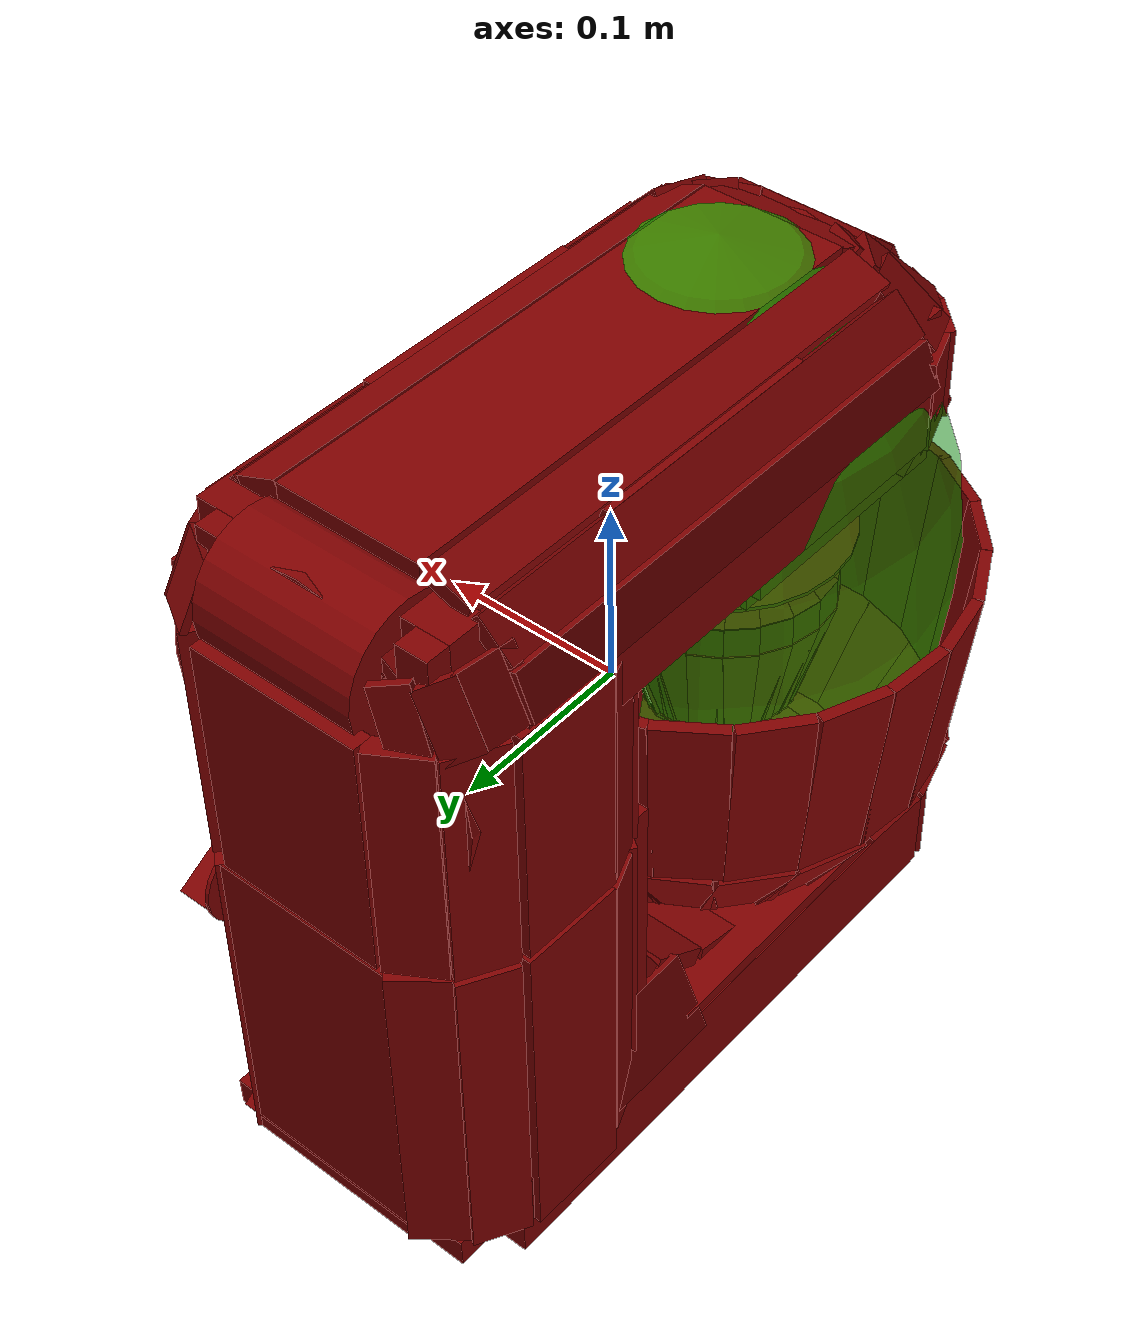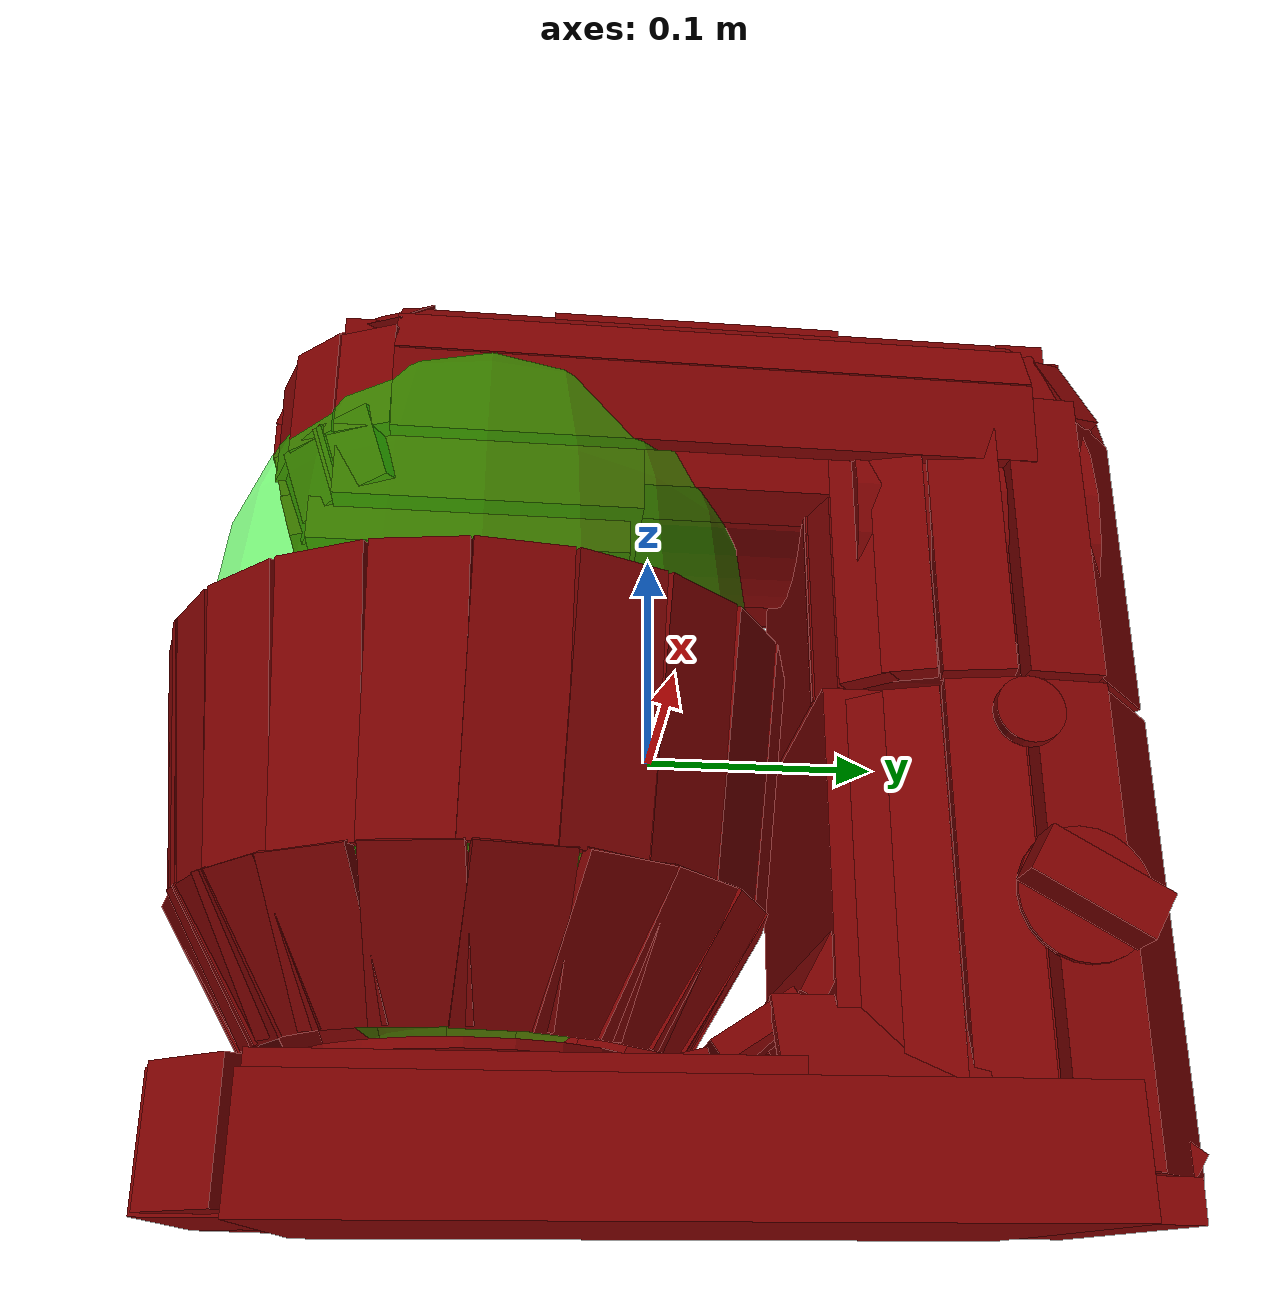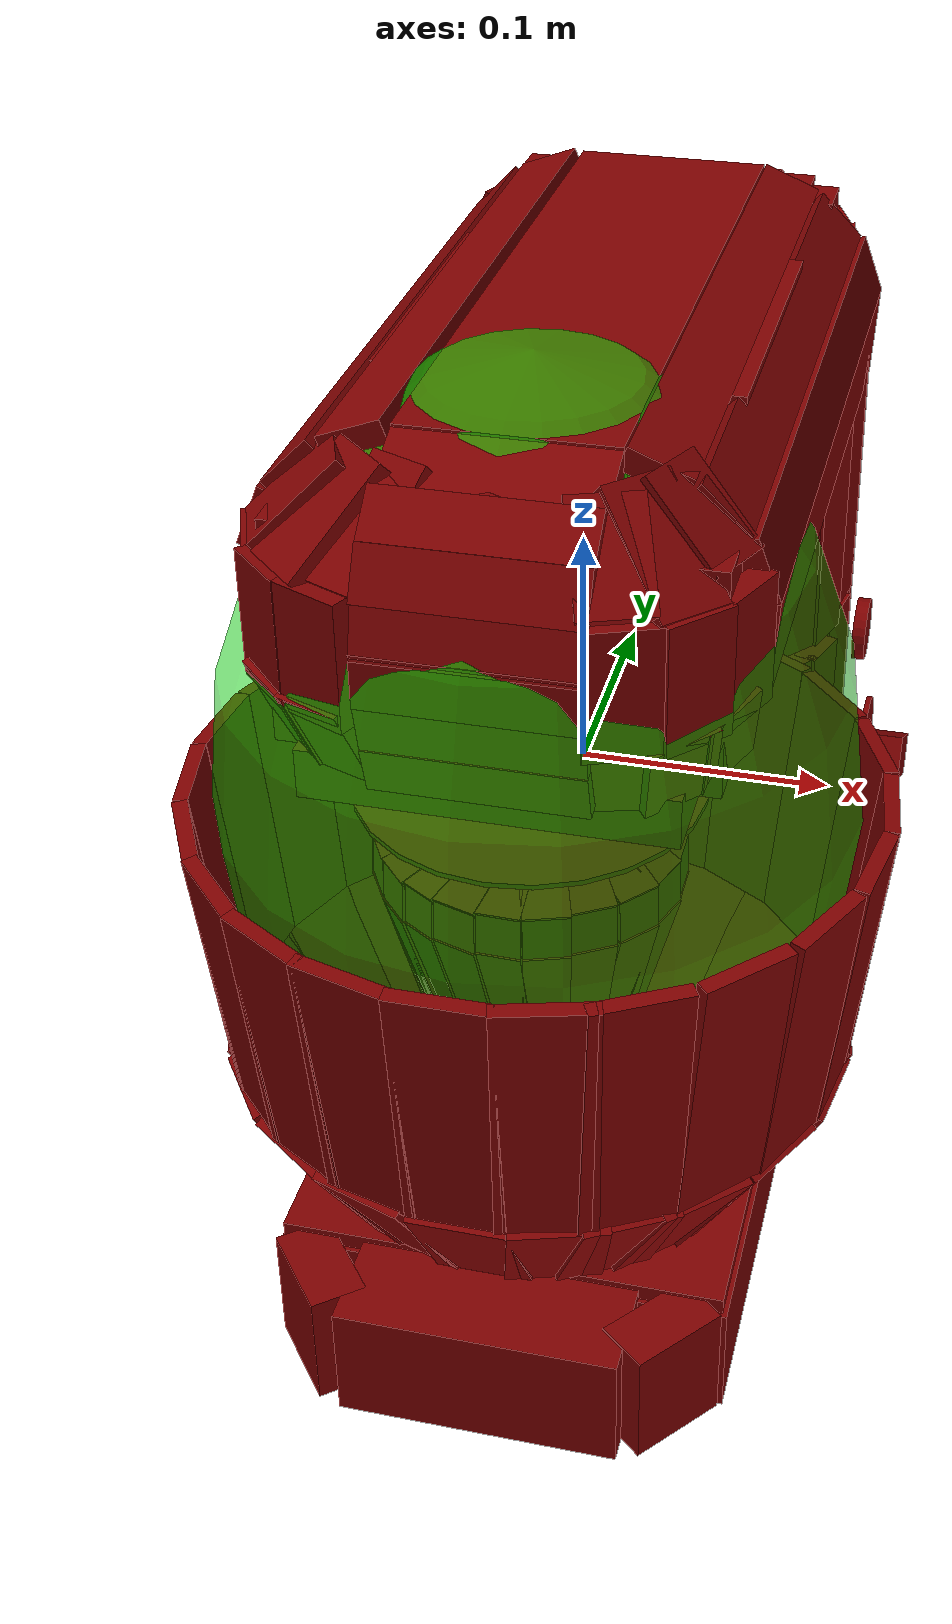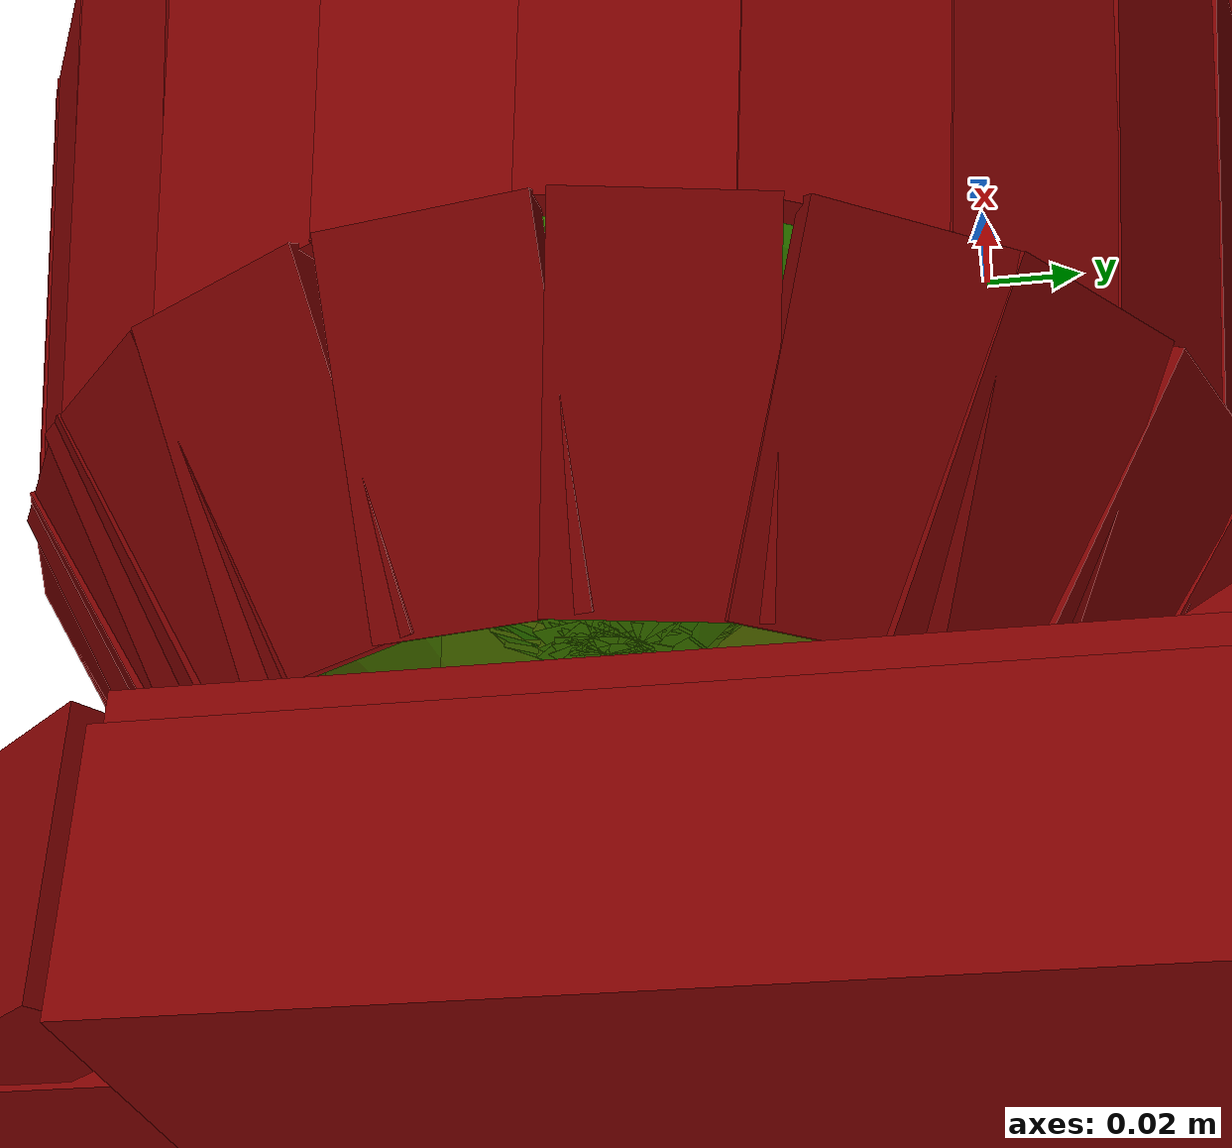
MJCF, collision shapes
<?xml version='1.0' encoding='UTF-8'?>
<mujoco model="model">
  <option timestep="0.002" gravity="0.0 0.0 -9.81"/>
  <compiler angle="radian"/>
  <asset>
    <mesh file="visuals/blender.obj" name="blender_vis"/>
    <mesh file="visuals/bowl.obj" name="bowl_vis"/>
    <mesh file="visuals/button_head_lock.obj" name="button_head_lock_vis"/>
    <mesh file="visuals/head.obj" name="head_vis"/>
    <mesh file="visuals/knob_speed.obj" name="knob_speed_vis"/>
    <mesh file="visuals/Body001.obj" name="Body001_vis"/>
    <texture file="visuals/T_BC001.png" name="Body001_material" type="2d"/>
    <material name="Body001_material" rgba="1 1 1 1.0" texture="Body001_material" shininess="0.1" specular="0.9"/>
    <texture file="visuals/T_BC001.png" name="bowl_material" type="2d"/>
    <material name="bowl_material" rgba="1 1 1 1.0" texture="bowl_material" shininess="0.1" specular="0.9"/>
    <texture file="visuals/T_BC001.png" name="button_head_lock_material" type="2d"/>
    <material name="button_head_lock_material" rgba="1 1 1 1.0" texture="button_head_lock_material" shininess="0.1" specular="0.9"/>
    <texture file="visuals/T_BC001.png" name="head_material" type="2d"/>
    <material name="head_material" rgba="1 1 1 1.0" texture="head_material" shininess="0.1" specular="0.9"/>
    <texture file="visuals/T_BC001.png" name="blender_material" type="2d"/>
    <material name="blender_material" rgba="1 1 1 1.0" texture="blender_material" shininess="0.1" specular="0.9"/>
    <texture file="visuals/T_BC001.png" name="knob_speed_material" type="2d"/>
    <material name="knob_speed_material" rgba="1 1 1 1.0" texture="knob_speed_material" shininess="0.1" specular="0.9"/>
  </asset>
  <default>
    <default class="visual">
      <geom conaffinity="0" contype="0" group="1" type="mesh"/>
    </default>
    <default class="collision">
      <geom group="0" rgba="0.5 0 0 0.5"/>
    </default>
    <default class="spawn">
      <geom group="0" rgba="1 1 1 0.5" contype="0" conaffinity="0"/>
      <site group="0" rgba="1 1 1 0.5"/>
    </default>
    <default class="region">
      <geom group="1" conaffinity="0" contype="0" rgba="0 1 0 0"/>
    </default>
  </default>
  <worldbody>
    <body>
      <body name="object">
        <geom mesh="Body001_vis" type="mesh" solimp="0.998 0.998 0.001" solref="0.001 1" friction="0.95 0.3 0.1" class="visual" material="Body001_material"/>
        <geom type="box" pos="0.00162704 0.01040870 -0.17253725" size="0.08990472555160522 0.160756453871727 0.024705523625016212" quat="1.0 0.0 0.0 0.0" class="collision"/>
        <geom type="cylinder" pos="-0.00675653 -0.07399403 -0.14183284" size="0.07319789379835129 0.002024284331128001" quat="1.0 0.0 0.0 0.0" class="collision"/>
        <geom type="box" pos="0.00279290 0.19319527 -0.17757623" size="0.055442556738853455 0.00843463372439146 0.014128785580396652" quat="0.9534308910369873 -0.30161160230636597 6.697122907492269e-17 1.2026518188257233e-23" class="collision"/>
        <geom type="box" pos="0.00279290 0.18161671 -0.18841621" size="0.07363889366388321 0.00843463372439146 0.014128785580396652" quat="0.6979237198829651 -0.7161720991134644 1.5902215080597956e-16 7.135739925789815e-24" class="collision"/>
        <geom type="box" pos="-0.00163558 0.20285030 -0.08490324" size="0.049669720232486725 0.005021312274038792 0.09460381418466568" quat="1.0 0.0 0.0 0.0" class="collision"/>
        <geom type="box" pos="-0.05904569 0.19667058 -0.08490324" size="0.014814227819442749 0.005021312274038792 0.09460443258285522" quat="0.9436448812484741 0.0 0.0 0.3309597671031952" class="collision"/>
        <geom type="box" pos="-0.07911258 0.17767885 -0.08490324" size="0.014814227819442749 0.005021311808377504 0.09460443258285522" quat="0.8611398339271545 0.0 0.0 0.5083681344985962" class="collision"/>
        <geom type="box" pos="-0.08749283 0.13634667 -0.08490324" size="0.027245767414569855 0.00502131087705493 0.09460443258285522" quat="0.7145032286643982 0.0 0.0 0.6996321678161621" class="collision"/>
        <geom type="box" pos="0.08317586 0.12575370 -0.08490324" size="0.014814227819442749 0.005021311808377504 0.09460443258285522" quat="0.6449642181396484 0.0 -0.0 -0.7642127871513367" class="collision"/>
        <geom type="box" pos="0.08358783 0.16096041 -0.08490324" size="0.016015637665987015 0.005043074022978544 0.09460443258285522" quat="0.7272552847862244 0.0 -0.0 -0.6863670349121094" class="collision"/>
        <geom type="box" pos="0.06389005 0.18900023 -0.08490324" size="0.02448882907629013 0.00502131087705493 0.09460443258285522" quat="0.9296313524246216 0.0 -0.0 -0.3684908449649811" class="collision"/>
        <geom type="box" pos="-0.00163558 0.07011864 -0.04418621" size="0.04967033118009567 0.005021312274038792 0.05387219786643982" quat="1.0 0.0 0.0 0.0" class="collision"/>
        <geom type="box" pos="-0.00163558 0.06484623 -0.09885083" size="0.06912857294082642 0.005021312274038792 0.019002310931682587" quat="0.9673065543174744 -0.25360992550849915 5.631270909715641e-17 8.218425880226234e-25" class="collision"/>
        <geom type="box" pos="-0.00163558 0.03531166 -0.12613799" size="0.06912857294082642 0.005021312739700079 0.019002310931682587" quat="0.8780341148376465 -0.47859808802604675 1.0627014322595361e-16 1.9115638012270297e-23" class="collision"/>
        <geom type="box" pos="-0.00163558 -0.00186804 -0.14405195" size="0.06912857294082642 0.005021311808377504 0.019002312794327736" quat="0.781984269618988 -0.623298168182373 1.3839999550455074e-16 2.208306610272578e-23" class="collision"/>
        <geom type="box" pos="-0.07251490 0.08190940 -0.07761785" size="0.011155763640999794 0.005021311342716217 0.08598798513412476" quat="0.955824613571167 0.0 -0.0 -0.293937623500824" class="collision"/>
        <geom type="box" pos="-0.08434413 0.10007720 -0.07761785" size="0.011155763640999794 0.00502131087705493 0.08598798513412476" quat="0.8310907483100891 0.0 -0.0 -0.5561368465423584" class="collision"/>
        <geom type="box" pos="-0.05728971 0.07432623 -0.07761785" size="0.011155763640999794 0.005021311342716217 0.08598798513412476" quat="0.9927864670753479 0.0 -0.0 -0.11989592015743256" class="collision"/>
        <geom type="box" pos="0.07241257 0.08330426 -0.08103223" size="0.011155763640999794 0.005021311342716217 0.08598798513412476" quat="0.9016786813735962 0.0 0.0 0.4324067234992981" class="collision"/>
        <geom type="box" pos="0.05335972 0.07296071 -0.08103223" size="0.011155763640999794 0.005021311342716217 0.08598798513412476" quat="0.9878917932510376 0.0 0.0 0.1551445871591568" class="collision"/>
        <geom type="box" pos="0.08118512 0.09787660 -0.08103223" size="0.011155763640999794 0.00502131087705493 0.08598798513412476" quat="0.8107764720916748 0.0 0.0 0.5853558778762817" class="collision"/>
        <geom type="box" pos="-0.08095876 0.07780278 -0.13479270" size="0.02172514796257019 0.038140490651130676 0.0026141840498894453" quat="0.8441252112388611 0.0 -0.5361461043357849 0.0" class="collision"/>
        <geom type="box" pos="0.07682744 0.07780278 -0.13431197" size="0.02172514796257019 0.038140490651130676 0.002614184282720089" quat="0.8749390244483948 0.0 0.48423314094543457 0.0" class="collision"/>
        <geom type="box" pos="0.00103302 -0.05000850 -0.14681241" size="0.0886635109782219 0.09841278195381165 0.005824797321110964" quat="1.0 0.0 0.0 0.0" class="collision"/>
        <geom type="box" pos="0.00103302 -0.16784243 -0.16932696" size="0.0555964894592762 0.01988396793603897 0.0256899893283844" quat="1.0 0.0 0.0 0.0" class="collision"/>
        <geom type="box" pos="-0.06766564 -0.16250904 -0.16932696" size="0.011214721947908401 0.01988396793603897 0.0256899893283844" quat="0.9411333203315735 0.0 0.0 0.33803555369377136" class="collision"/>
        <geom type="box" pos="0.06876694 -0.16250904 -0.16823488" size="0.011214721947908401 0.01988396793603897 0.0256899893283844" quat="0.33648473024368286 0.0 0.0 0.9416888952255249" class="collision"/>
        <geom type="box" pos="-0.00163558 0.12586572 -0.08490324" size="0.07255306839942932 0.061715446412563324 0.09460414946079254" quat="1.0 0.0 0.0 0.0" class="collision"/>
        <body name="bowl">
          <geom mesh="bowl_vis" type="mesh" solimp="0.998 0.998 0.001" solref="0.001 1" friction="0.95 0.3 0.1" class="visual" material="bowl_material"/>
          <geom type="box" pos="-0.00105462 -0.19896373 -0.01880190" size="0.018773013725876808 0.0029905198607593775 0.05602985620498657" quat="0.9985294938087463 0.05421159043908119 0.0 0.0" class="collision"/>
          <geom type="box" pos="-0.03463005 -0.19407371 -0.01880458" size="0.018773015588521957 0.002990520093590021 0.05602986365556717" quat="0.9891883730888367 0.05370444804430008 -0.007397891487926245 -0.13626262545585632" class="collision"/>
          <geom type="box" pos="-0.06489580 -0.18076912 -0.01880964" size="0.018773013725876808 0.0029905205592513084 0.056029871106147766" quat="0.9622957706451416 0.05224435776472092 -0.01447127666324377 -0.266548216342926" class="collision"/>
          <geom type="box" pos="-0.09127066 -0.15926026 -0.01881701" size="0.018773017451167107 0.002990520093590021 0.05602985620498657" quat="0.9167933464050293 0.04977397248148918 -0.021481214091181755 -0.39566531777381897" class="collision"/>
          <geom type="box" pos="-0.11082070 -0.13146533 -0.01882597" size="0.01877301000058651 0.002990520093590021 0.05602986365556717" quat="0.8542089462280273 0.04637617990374565 -0.02807384729385376 -0.5170959234237671" class="collision"/>
          <geom type="box" pos="-0.12250508 -0.09756235 -0.01883645" size="0.01877301000058651 0.002990520792081952 0.056029871106147766" quat="0.7708883881568909 0.041852597147226334 -0.0344565212726593 -0.6346591114997864" class="collision"/>
          <geom type="box" pos="-0.12406020 -0.06180202 -0.01884710" size="0.01877301000058651 0.0029905198607593775 0.056029871106147766" quat="0.6717950701713562 0.036472681909799576 -0.04010780155658722 -0.7387506365776062" class="collision"/>
          <geom type="box" pos="-0.11547022 -0.02727455 -0.01885701" size="0.01877300813794136 0.002990520093590021 0.05602985620498657" quat="0.5595933794975281 0.030381105840206146 -0.044898562133312225 -0.8269923329353333" class="collision"/>
          <geom type="box" pos="-0.09677899 0.00428396 -0.01886564" size="0.018773013725876808 0.0029905198607593775 0.05602985620498657" quat="0.4320467412471771 0.02345641888678074 -0.04887421429157257 -0.9002203941345215" class="collision"/>
          <geom type="box" pos="-0.06989275 0.02891354 -0.01887194" size="0.01877301000058651 0.002990520093590021 0.05602985620498657" quat="0.29604005813598633 0.016072439029812813 -0.0517742820084095 -0.9536358714103699" class="collision"/>
          <geom type="box" pos="-0.03802406 0.04439542 -0.01887535" size="0.018773013725876808 0.0029905205592513084 0.056029871106147766" quat="0.15786147117614746 0.008570518344640732 -0.053529784083366394 -0.9859720468521118" class="collision"/>
          <geom type="box" pos="-0.00386284 0.05026384 -0.01887584" size="0.01877300813794136 0.0029905198607593775 0.05602985620498657" quat="0.01961621083319187 0.0010649911127984524 -0.05420108139514923 -0.9983367919921875" class="collision"/>
          <geom type="box" pos="0.03334792 0.04576601 -0.01887317" size="0.018773013725876808 0.002990520093590021 0.05602986365556717" quat="0.13031423091888428 0.007074955850839615 0.0537479966878891 0.9899895191192627" class="collision"/>
          <geom type="box" pos="0.06679551 0.03088547 -0.01886757" size="0.01877301000058651 0.0029905205592513084 0.05602986365556717" quat="0.2739492654800415 0.014873085543513298 0.05213141068816185 0.9602150321006775" class="collision"/>
          <geom type="box" pos="0.09466445 0.00671158 -0.01885942" size="0.018773013725876808 0.002990520792081952 0.05602986365556717" quat="0.4127850830554962 0.02241067960858345 0.04936249181628227 0.9092137217521667" class="collision"/>
          <geom type="box" pos="0.11418916 -0.02445274 -0.01884951" size="0.01877300813794136 0.002990518929436803 0.05602985620498657" quat="0.5422492623329163 0.029439471662044525 0.04552154615521431 0.8384669423103333" class="collision"/>
          <geom type="box" pos="0.12370987 -0.05944992 -0.01883879" size="0.01877301000058651 0.002990519627928734 0.05602985620498657" quat="0.6584212779998779 0.03574661910533905 0.04075627774000168 0.7506946921348572" class="collision"/>
          <geom type="box" pos="0.12282670 -0.09527522 -0.01882821" size="0.01877300813794136 0.002990520792081952 0.05602985620498657" quat="0.7595313787460327 0.041236039251089096 0.03519212454557419 0.6482077240943909" class="collision"/>
          <geom type="box" pos="0.11142690 -0.13009420 -0.01881827" size="0.018773017451167107 0.002990520093590021 0.056029871106147766" quat="0.8466377854347229 0.04596516862511635 0.028741935268044472 0.5294011235237122" class="collision"/>
          <geom type="box" pos="0.08991104 -0.16060324 -0.01880999" size="0.018773013725876808 0.00299051939509809 0.05602986365556717" quat="0.9164795279502869 0.04975699633359909 0.021520676091313362 0.39639171957969666" class="collision"/>
          <geom type="box" pos="0.06028794 -0.18339306 -0.01880428" size="0.018773013725876808 0.002990520792081952 0.056029871106147766" quat="0.9656398892402649 0.05242596194148064 0.013799061067402363 0.2541666626930237" class="collision"/>
          <geom type="box" pos="0.03227629 -0.19470432 -0.01880194" size="0.018773015588521957 0.002990520093590021 0.056029871106147766" quat="0.9893670678138733 0.05371414124965668 0.007327110506594181 0.1349589079618454" class="collision"/>
          <geom type="box" pos="-0.00105462 -0.17737210 -0.10290205" size="0.018773015588521957 0.0027088394854217768 0.034455206245183945" quat="0.9623625874519348 0.271768718957901 0.0 0.0" class="collision"/>
          <geom type="box" pos="-0.03421032 -0.17153084 -0.10293578" size="0.018773017451167107 0.002708839252591133 0.03447578847408295" quat="0.9493533968925476 0.2680949568748474 -0.04453460872173309 -0.15770187973976135" class="collision"/>
          <geom type="box" pos="-0.06116750 -0.15705426 -0.10322208" size="0.018773015588521957 0.0027088394854217768 0.0347813256084919" quat="0.9152575135231018 0.25846636295318604 -0.08398435264825821 -0.29739782214164734" class="collision"/>
          <geom type="box" pos="-0.08417615 -0.13334788 -0.10336152" size="0.018773015588521957 0.002708839252591133 0.034901391714811325" quat="0.8554472923278809 0.24157610535621643 -0.12449585646390915 -0.4408533573150635" class="collision"/>
          <geom type="box" pos="-0.09873985 -0.10260190 -0.10351995" size="0.018773015588521957 0.002708838786929846 0.03503530099987984" quat="0.7705292701721191 0.21759547293186188 -0.1628202646970749 -0.576564371585846" class="collision"/>
          <geom type="box" pos="-0.10235675 -0.06960243 -0.10390279" size="0.018773015588521957 0.002708838554099202 0.035432346165180206" quat="0.667048454284668 0.18837277591228485 -0.19589264690876007 -0.6936772465705872" class="collision"/>
          <geom type="box" pos="-0.09501288 -0.03599562 -0.10389825" size="0.01877301000058651 0.002708838554099202 0.03537725284695625" quat="0.541220486164093 0.15283925831317902 -0.22471848130226135 -0.7957525849342346" class="collision"/>
          <geom type="box" pos="-0.07826885 -0.00796983 -0.10360870" size="0.018773015588521957 0.002708838786929846 0.03499946743249893" quat="0.407856822013855 0.1151777133345604 -0.24615508317947388 -0.8716619610786438" class="collision"/>
          <geom type="box" pos="-0.05243288 0.01367816 -0.10385150" size="0.018773015588521957 0.002708838554099202 0.03525856137275696" quat="0.25940626859664917 0.07325565069913864 -0.26170945167541504 -0.9267417192459106" class="collision"/>
          <geom type="box" pos="-0.02173235 0.02619338 -0.10315969" size="0.018773015588521957 0.002708838088437915 0.034437429159879684" quat="0.10678956657648087 0.03015711158514023 -0.2700902223587036 -0.9564192891120911" class="collision"/>
          <geom type="box" pos="0.01145383 0.02783381 -0.10319442" size="0.018773015588521957 0.002708839951083064 0.03448551520705223" quat="0.04864132031798363 0.01373619120568037 0.27142131328582764 0.9611325860023499" class="collision"/>
          <geom type="box" pos="0.04358084 0.01868342 -0.10330831" size="0.018773017451167107 0.0027088397182524204 0.034642696380615234" quat="0.20373256504535675 0.057533543556928635 0.2656089663505554 0.9405502676963806" class="collision"/>
          <geom type="box" pos="0.07095583 -0.00002717 -0.10325135" size="0.01877301186323166 0.002708839252591133 0.03461287543177605" quat="0.3524662256240845 0.09953554719686508 0.252885103225708 0.8954939246177673" class="collision"/>
          <geom type="box" pos="0.09020219 -0.02498090 -0.10311591" size="0.01877300813794136 0.0027088383212685585 0.034498170018196106" quat="0.48533061146736145 0.13705609738826752 0.23467819392681122 0.8310210704803467" class="collision"/>
          <geom type="box" pos="0.10164126 -0.05759543 -0.10280900" size="0.01877301186323166 0.002708839252591133 0.03419177606701851" quat="0.617851197719574 0.17447955906391144 0.20836293697357178 0.7378358244895935" class="collision"/>
          <geom type="box" pos="0.10189045 -0.09098008 -0.10244548" size="0.018773015588521957 0.0027088394854217768 0.033816687762737274" quat="0.7291343212127686 0.20590564608573914 0.1773727536201477 0.6280962824821472" class="collision"/>
          <geom type="box" pos="0.09073392 -0.12395351 -0.10218533" size="0.01877301186323166 0.002708839252591133 0.03355877473950386" quat="0.8245988488197327 0.23286457359790802 0.1401153802871704 0.49616381525993347" class="collision"/>
          <geom type="box" pos="0.07133070 -0.14920202 -0.10222540" size="0.018773017451167107 0.0027088394854217768 0.03363889455795288" quat="0.8912619352340698 0.25169000029563904 0.10251995921134949 0.3630344271659851" class="collision"/>
          <geom type="box" pos="0.03003175 -0.17296278 -0.10277801" size="0.018773017451167107 0.002708839252591133 0.034312114119529724" quat="0.9510646462440491 0.2685782015323639 0.04152083024382591 0.1470297873020172" class="collision"/>
          <geom type="box" pos="0.05093202 -0.16404009 -0.10266143" size="0.01877300813794136 0.002708838554099202 0.034167684614658356" quat="0.9289951920509338 0.26234591007232666 0.07094284892082214 0.25121641159057617" class="collision"/>
          <geom type="cylinder" pos="0.00069033 -0.07399403 -0.13563533" size="0.07319789379835129 0.002024284331128001" quat="1.0 0.0 0.0 0.0" class="collision"/>
          <geom name="reg_bowl" type="ellipsoid" pos="0.00044902 -0.07432259 0.03781115" size="0.1205388531088829 0.12162107229232788 0.1706704944372177" rgba="0 1 0 0.5" class="region"/>
        </body>
        <body name="button_head_lock">
          <joint axis="-1.0 0.0 0.0" pos="0.09684014 0.13995723 -0.00772063" limited="true" name="button_head_lock_joint" range="0.0 0.004" type="slide" damping="1" frictionloss="1" armature=".01" stiffness="0.05"/>
          <geom mesh="button_head_lock_vis" type="mesh" solimp="0.998 0.998 0.001" solref="0.001 1" friction="0.95 0.3 0.1" class="visual" material="button_head_lock_material"/>
          <geom class="collision" type="cylinder" pos="0.09696207 0.13985719 -0.00783222" size="0.013906983658671379 0.0027774162590503693" quat="0.7071068286895752 -0.0 0.7071067690849304 0.0" name="button_head_lock_main"/>
        </body>
        <body name="head">
          <joint axis="-1.0 0.0 0.0" pos="0.00576755 0.21019583 0.01351245" limited="true" name="head_joint" range="0.0 1.5707963267948966" type="hinge" damping="1" frictionloss="1" armature=".01" stiffness="0.05"/>
          <geom mesh="head_vis" type="mesh" solimp="0.998 0.998 0.001" solref="0.001 1" friction="0.95 0.3 0.1" class="visual" material="head_material"/>
          <geom type="box" pos="0.00056514 -0.08114891 0.07859270" size="0.06693771481513977 0.06693771481513977 0.009613923728466034" quat="1.0 0.0 0.0 0.0" class="collision"/>
          <geom type="box" pos="0.00799922 -0.09375625 0.06265179" size="0.029878204688429832 0.014719265513122082 0.005266072228550911" quat="0.8704594373703003 -7.596937479092958e-08 2.9401514112237237e-08 -0.49224016070365906" class="collision"/>
          <geom type="box" pos="-0.00163558 0.20370638 0.07806139" size="0.04505390673875809 0.005021312274038792 0.06495030224323273" quat="1.0 0.0 0.0 0.0" class="collision"/>
          <geom type="box" pos="-0.05907651 0.19670910 0.07806139" size="0.014814228750765324 0.00502131087705493 0.06495030224323273" quat="0.9627028703689575 0.0 0.0 0.2705608308315277" class="collision"/>
          <geom type="box" pos="-0.07911258 0.17767885 0.07806139" size="0.014814227819442749 0.005021311342716217 0.06495030224323273" quat="0.8611398339271545 0.0 0.0 0.5083681344985962" class="collision"/>
          <geom type="box" pos="-0.08749283 0.13634667 0.07806139" size="0.027245767414569855 0.00502131087705493 0.06495030224323273" quat="0.7145032286643982 0.0 0.0 0.6996321678161621" class="collision"/>
          <geom type="box" pos="0.08317586 0.12575370 0.07806139" size="0.014814227819442749 0.005021311808377504 0.06495030224323273" quat="0.6449642181396484 0.0 -0.0 -0.7642127871513367" class="collision"/>
          <geom type="box" pos="0.08358783 0.16096041 0.07806139" size="0.016015637665987015 0.005043073557317257 0.06495030224323273" quat="0.7272552847862244 0.0 -0.0 -0.6863670349121094" class="collision"/>
          <geom type="box" pos="0.06689835 0.18660274 0.07806139" size="0.023743215948343277 0.00502131087705493 0.06495030224323273" quat="0.9296313524246216 0.0 -0.0 -0.3684908449649811" class="collision"/>
          <geom type="box" pos="-0.00163558 0.07011864 0.07621478" size="0.049669720232486725 0.005021312274038792 0.06262287497520447" quat="1.0 0.0 0.0 0.0" class="collision"/>
          <geom type="box" pos="-0.07251490 0.08190940 0.07642115" size="0.011155763640999794 0.005021311808377504 0.061475761234760284" quat="0.955824613571167 0.0 -0.0 -0.293937623500824" class="collision"/>
          <geom type="box" pos="-0.08434413 0.10007720 0.07642115" size="0.011155763640999794 0.00502131087705493 0.061475761234760284" quat="0.8310907483100891 0.0 -0.0 -0.5561368465423584" class="collision"/>
          <geom type="box" pos="-0.05728971 0.07432623 0.07642115" size="0.011155763640999794 0.005021311342716217 0.061475761234760284" quat="0.9927864670753479 0.0 -0.0 -0.11989592015743256" class="collision"/>
          <geom type="box" pos="0.07241257 0.08330426 0.07398009" size="0.011155763640999794 0.005021311342716217 0.061475761234760284" quat="0.9016786813735962 0.0 0.0 0.4324067234992981" class="collision"/>
          <geom type="box" pos="0.05335972 0.07296071 0.07398009" size="0.011155763640999794 0.005021311808377504 0.061475761234760284" quat="0.9878917932510376 0.0 0.0 0.1551445871591568" class="collision"/>
          <geom type="box" pos="0.08118512 0.09787660 0.07398009" size="0.011155763640999794 0.00502131087705493 0.061475761234760284" quat="0.8107764720916748 0.0 0.0 0.5853558778762817" class="collision"/>
          <geom type="cylinder" pos="0.00023489 0.13252060 0.09853985" size="0.08380713313817978 0.05254381522536278" quat="0.7071067094802856 0.7071068286895752 0.0 0.0" class="collision"/>
          <geom type="cylinder" pos="0.00145609 0.02262078 0.13603958" size="0.05096551775932312 0.16331139206886292" quat="0.7071067094802856 0.7071068286895752 0.0 0.0" class="collision"/>
          <geom type="box" pos="0.00141370 0.02118313 0.19234517" size="0.03828424587845802 0.13630065321922302 0.004347546491771936" quat="1.0 0.0 0.0 0.0" class="collision"/>
          <geom type="box" pos="0.05023256 0.02118312 0.18849105" size="0.011963212862610817 0.13630065321922302 0.004347546026110649" quat="0.9812838435173035 4.2135749252371736e-16 0.1925669014453888 2.5873070796933462e-08" class="collision"/>
          <geom type="box" pos="0.07025460 0.02118312 0.17527398" size="0.011963212862610817 0.13630065321922302 0.004347546026110649" quat="0.9243265986442566 -4.5678115153172105e-15 0.38160234689712524 5.1271651813067365e-08" class="collision"/>
          <geom type="box" pos="0.08375944 0.02118312 0.15714420" size="0.011963211931288242 0.13630065321922302 0.004347546026110649" quat="0.8209965229034424 -7.004454677541185e-15 0.5709332227706909 7.67099450627029e-08" class="collision"/>
          <geom type="box" pos="0.08644705 0.02118313 0.12886643" size="0.01816057227551937 0.13630065321922302 0.004347546026110649" quat="0.684807300567627 -2.199850301920492e-09 0.7287241816520691 9.574515047461318e-08" class="collision"/>
          <geom type="box" pos="-0.08498380 0.02118312 0.15605417" size="0.011963212862610817 0.13630065321922302 0.004347546026110649" quat="0.8300378322601318 2.5845179623973933e-15 -0.5577071309089661 -7.493287057513953e-08" class="collision"/>
          <geom type="box" pos="-0.07176673 0.02118312 0.17607622" size="0.011963212862610817 0.13630065321922302 0.004347546026110649" quat="0.9234311580657959 -7.019975709266673e-15 -0.3837641179561615 -5.15621039198777e-08" class="collision"/>
          <geom type="box" pos="-0.05030699 0.02118312 0.18935907" size="0.011963212862610817 0.13630065321922302 0.004347546026110649" quat="0.9842429161071777 -1.7078779525597082e-14 -0.17682145535945892 -2.3757507960908697e-08" class="collision"/>
          <geom type="box" pos="-0.08618467 0.02118313 0.13015725" size="0.004447557497769594 0.13630065321922302 0.01732444390654564" quat="1.0 0.0 0.0 0.0" class="collision"/>
          <geom type="cylinder" pos="0.00145609 0.16874729 0.15361039" size="0.03575201332569122 0.042757969349622726" quat="0.4999999701976776 0.5 0.5 0.5" class="collision"/>
          <geom type="box" pos="-0.08097895 0.16434318 0.16009460" size="0.017529677599668503 0.014469706453382969 0.0016807245556265116" quat="0.8362656235694885 -0.09358292818069458 -0.536928117275238 -0.060085441917181015" class="collision"/>
          <geom type="box" pos="-0.07352199 0.18332414 0.15668137" size="0.01752968318760395 0.00930290948599577 0.002278650412335992" quat="0.7895967364311218 -0.29092079401016235 -0.5069642066955566 -0.18678711354732513" class="collision"/>
          <geom type="box" pos="-0.05847341 0.19411938 0.15480776" size="0.017529679462313652 0.00930290948599577 0.002278650412335992" quat="0.6993736028671265 -0.409210205078125 -0.49341464042663574 -0.3161732852458954" class="collision"/>
          <geom type="box" pos="0.05933657 0.19178008 0.15828101" size="0.017529677599668503 0.014469705522060394 0.0016807245556265116" quat="0.4333280622959137 -0.492570161819458 -0.23328997194766998 -0.7177584767341614" class="collision"/>
          <geom type="box" pos="0.07473029 0.17840411 0.15486778" size="0.0175296813249588 0.00930290948599577 0.002278650412335992" quat="0.30291128158569336 -0.5819306969642639 -0.05481088161468506 -0.7527264952659607" class="collision"/>
          <geom type="box" pos="0.07987060 0.16061159 0.15299417" size="0.0175296813249588 0.00930290948599577 0.002278650179505348" quat="0.14517681300640106 -0.6390992403030396 0.049629390239715576 -0.7536662220954895" class="collision"/>
          <geom type="box" pos="0.05515616 0.16282488 0.15520062" size="0.014362861402332783 0.010855750180780888 0.02878350391983986" quat="1.0 0.0 0.0 0.0" class="collision"/>
          <geom type="box" pos="0.04921015 0.17920223 0.15520062" size="0.00840244721621275 0.006780486553907394 0.02878350391983986" quat="1.0 0.0 0.0 0.0" class="collision"/>
          <geom type="box" pos="-0.05225156 0.16282488 0.15520062" size="0.014362861402332783 0.010855750180780888 0.02878350391983986" quat="1.0 0.0 0.0 0.0" class="collision"/>
          <geom type="box" pos="-0.05819757 0.17920223 0.15520062" size="0.008402453735470772 0.006780486553907394 0.02878350391983986" quat="1.0 0.0 0.0 0.0" class="collision"/>
          <geom type="box" pos="0.00103302 -0.07357082 0.12659851" size="0.07779024541378021 0.06399105489253998 0.04254274070262909" quat="1.0 0.0 0.0 0.0" class="collision"/>
          <geom type="box" pos="0.00103302 0.01567212 0.14453678" size="0.06687738746404648 0.0639912411570549 0.04254274070262909" quat="1.0 0.0 0.0 0.0" class="collision"/>
          <geom type="box" pos="0.00141370 -0.11944231 0.17287062" size="0.03828424587845802 0.013255536556243896 0.019374029710888863" quat="0.9806175231933594 0.19593189656734467 -4.3505620565508144e-17 2.6379463311088585e-24" class="collision"/>
          <geom type="box" pos="0.00141370 -0.13652015 0.16782199" size="0.03828424587845802 0.009861667640507221 0.018606586381793022" quat="0.9398419260978699 0.3416096866130829 -7.585258790256575e-17 -8.535439495750613e-25" class="collision"/>
          <geom type="box" pos="0.00141370 -0.14551739 0.15864332" size="0.03828424587845802 0.009861668571829796 0.018154846504330635" quat="0.8608698844909668 0.5088251829147339 -1.1298188671620888e-16 -3.3041172774626567e-24" class="collision"/>
          <geom type="box" pos="0.00141370 -0.15144463 0.14479782" size="0.03828424587845802 0.009861668571829796 0.01588960364460945" quat="0.8030709624290466 0.5958834290504456 -1.323127005848791e-16 -4.366051654141558e-24" class="collision"/>
          <geom type="box" pos="0.00141370 -0.15333310 0.13206328" size="0.03828424587845802 0.01589028909802437 0.009990944527089596" quat="1.0 0.0 0.0 0.0" class="collision"/>
          <geom type="box" pos="0.00141370 -0.15277693 0.11619994" size="0.03828424587845802 0.009861668571829796 0.01418495923280716" quat="0.6199234127998352 0.7846623063087463 -1.7423003180388948e-16 -1.4786541336094722e-23" class="collision"/>
          <geom type="box" pos="0.00141370 -0.14755060 0.09804349" size="0.03828424587845802 0.009861668571829796 0.01495105866342783" quat="0.5950084328651428 0.8037194609642029 -1.7846158341524535e-16 -2.403919502307146e-23" class="collision"/>
          <geom type="box" pos="-0.08262083 -0.12411797 0.13497095" size="0.013216618448495865 0.00464509567245841 0.023897482082247734" quat="0.8223839998245239 0.0 -0.0 -0.568932831287384" class="collision"/>
          <geom type="box" pos="-0.07123011 -0.14573291 0.13497095" size="0.01321661751717329 0.00464509567245841 0.023897482082247734" quat="0.9277811050415039 0.0 -0.0 -0.373124897480011" class="collision"/>
          <geom type="box" pos="-0.05106021 -0.15896539 0.13497095" size="0.013216618448495865 0.00464509567245841 0.023897482082247734" quat="0.9782099723815918 0.0 -0.0 -0.20761796832084656" class="collision"/>
          <geom type="box" pos="0.04873896 -0.15848601 0.13497095" size="0.01321661751717329 0.00464509567245841 0.023897482082247734" quat="0.9818600416183472 0.0 0.0 0.18960721790790558" class="collision"/>
          <geom type="box" pos="0.06925045 -0.14585192 0.13497095" size="0.01321661751717329 0.00464509567245841 0.023897482082247734" quat="0.9156820178031921 0.0 0.0 0.40190356969833374" class="collision"/>
          <geom type="box" pos="0.08122881 -0.12548999 0.13497095" size="0.01321661751717329 0.00464509567245841 0.023897482082247734" quat="0.8326998949050903 0.0 0.0 0.5537245273590088" class="collision"/>
          <geom type="box" pos="-0.06571316 -0.12411088 0.17306149" size="0.01321661751717329 0.00464509567245841 0.020833054557442665" quat="0.7545230388641357 -0.32712462544441223 0.22630777955055237 -0.5219858884811401" class="collision"/>
          <geom type="box" pos="-0.05327172 -0.13704947 0.17305186" size="0.01321661751717329 0.00464509567245841 0.023897482082247734" quat="0.8512229919433594 -0.3690491318702698 0.14842009544372559 -0.3423355221748352" class="collision"/>
          <geom type="box" pos="-0.03537374 -0.14222078 0.17289390" size="0.010962706990540028 0.004645095206797123 0.023897482082247734" quat="0.8974906206130981 -0.38910841941833496 0.0825854241847992 -0.190485879778862" class="collision"/>
          <geom type="box" pos="0.04192262 -0.14502819 0.17284547" size="0.01321661751717329 0.004645096138119698 0.020546825602650642" quat="0.9025411605834961 -0.39129820466041565 -0.07149488478899002 0.1649051159620285" class="collision"/>
          <geom type="box" pos="0.05578573 -0.13515904 0.17295931" size="0.01321661751717329 0.00464509567245841 0.023897482082247734" quat="0.8437832593917847 -0.3658235967159271 -0.15620142221450806 0.3602833151817322" class="collision"/>
          <geom type="box" pos="0.06422902 -0.11874649 0.17666455" size="0.013216616585850716 0.004645094741135836 0.019503479823470116" quat="0.7690514922142029 -0.3334234356880188 -0.21692053973674774 0.5003339648246765" class="collision"/>
          <geom type="box" pos="-0.07667224 -0.12632708 0.10722865" size="0.01321661937981844 0.00464509567245841 0.0175640769302845" quat="0.808824896812439 0.20893988013267517 0.015132883563637733 -0.5494701266288757" class="collision"/>
          <geom type="box" pos="-0.06701197 -0.14318491 0.10284761" size="0.013216616585850716 0.00464509567245841 0.01756407879292965" quat="0.9102560877799988 0.20711825788021088 -0.03141559287905693 -0.3571399748325348" class="collision"/>
          <geom type="box" pos="-0.04956074 -0.15408967 0.10253273" size="0.013216618448495865 0.00464509567245841 0.01756407506763935" quat="0.9581919312477112 0.19860298931598663 -0.06664641946554184 -0.19489312171936035" class="collision"/>
          <geom type="box" pos="0.04718849 -0.15142028 0.09972328" size="0.013216620311141014 0.004645096138119698 0.015986895188689232" quat="0.9753819704055786 0.16564033925533295 0.03299707546830177 0.14179013669490814" class="collision"/>
          <geom type="box" pos="0.06455880 -0.14446703 0.09998590" size="0.013216618448495865 0.004645096138119698 0.01598690077662468" quat="0.9199314117431641 0.1688370257616043 -0.004424192477017641 0.35383716225624084" class="collision"/>
          <geom type="box" pos="0.07664261 -0.12941337 0.10356821" size="0.013216614723205566 0.004645096138119698 0.015986895188689232" quat="0.8451710343360901 0.16554726660251617 -0.03346046805381775 0.5071098804473877" class="collision"/>
          <body name="blender">
            <joint axis="0.0 0.0 1.0" pos="-0.00101584 -0.08209574 -0.00065528" limited="false" name="blender_joint" range="0 360" type="hinge" damping="1" frictionloss="1" armature=".01" stiffness="0.05"/>
            <geom mesh="blender_vis" type="mesh" solimp="0.998 0.998 0.001" solref="0.001 1" friction="0.95 0.3 0.1" class="visual" material="blender_material"/>
            <geom type="cylinder" pos="-0.00077035 -0.08211017 0.04033605" size="0.00644986005499959 0.013895629905164242" quat="1.0 0.0 0.0 0.0" class="collision"/>
            <geom type="cylinder" pos="-0.00077035 -0.08211017 0.04265423" size="0.06606562435626984 0.0009801468113437295" quat="1.0 0.0 0.0 0.0" class="collision"/>
            <geom type="box" pos="0.04510030 -0.09663315 -0.02839297" size="0.0020608543418347836 0.008796794340014458 0.034217726439237595" quat="0.9778345823287964 0.021900562569499016 0.13528378307819366 -0.15829776227474213" class="collision"/>
            <geom type="box" pos="0.03119155 -0.09200870 -0.06753787" size="0.00206085410900414 0.008796795271337032 0.00875120423734188" quat="0.913358211517334 0.06062386929988861 0.374485045671463 -0.14785979688167572" class="collision"/>
            <geom type="box" pos="0.01909349 -0.08798628 -0.07804897" size="0.00206085410900414 0.008796793408691883 0.00875120423734188" quat="0.8596978783607483 0.0785408467054367 0.48516160249710083 -0.13917295634746552" class="collision"/>
            <geom type="box" pos="0.00507395 -0.08332498 -0.08308075" size="0.00206085410900414 0.008796794340014458 0.00875120423734188" quat="0.7033998966217041 0.11212606728076935 0.6925957202911377 -0.11387508362531662" class="collision"/>
            <geom type="box" pos="0.05323678 -0.09933843 0.01318462" size="0.0020608543418347836 0.008796793408691883 0.008751205168664455" quat="0.9869764447212219 -0.002984000602737069 -0.018432721495628357 -0.15977759659290314" class="collision"/>
            <geom type="box" pos="0.04703974 -0.09727800 0.02399758" size="0.00206085410900414 0.008796794340014458 0.00875120423734188" quat="0.8303229212760925 -0.08642740547657013 -0.5338783264160156 -0.13441769778728485" class="collision"/>
            <geom type="box" pos="0.03180109 -0.09221137 0.02870818" size="0.00206085410900414 0.008796794340014458 0.00875120423734188" quat="0.7296223044395447 -0.10764100402593613 -0.6649159789085388 -0.11811623722314835" class="collision"/>
            <geom type="box" pos="0.01808632 -0.08765142 0.02956466" size="0.00206085410900414 0.008796795271337032 0.00875120423734188" quat="0.7151980996131897 -0.1101490780711174 -0.6804068684577942 -0.11578144133090973" class="collision"/>
            <geom type="box" pos="0.04670697 -0.08258589 -0.02839297" size="0.0020608543418347836 0.008796795271337032 0.034217726439237595" quat="0.9905504584312439 -0.000738514878321439 0.1370430290699005 0.005338022951036692" class="collision"/>
            <geom type="box" pos="0.03205044 -0.08274385 -0.06753787" size="0.00206085410900414 0.008796795271337032 0.00875120423734188" quat="0.9252355694770813 -0.002044317778199911 0.379354864358902 0.004986082669347525" class="collision"/>
            <geom type="box" pos="0.01930194 -0.08288126 -0.07804897" size="0.00206085410900414 0.008796795271337032 0.00875120423734188" quat="0.8708774447441101 -0.002648495603352785 0.49147066473960876 0.004693153779953718" class="collision"/>
            <geom type="box" pos="0.00452866 -0.08304048 -0.08308075" size="0.0020608543418347836 0.008796794340014458 0.00875120423734188" quat="0.7125478982925415 -0.0037810932844877243 0.7016028165817261 0.003840172430500388" class="collision"/>
            <geom type="box" pos="0.05528091 -0.08249348 0.01318462" size="0.00206085410900414 0.008796795271337032 0.008751205168664455" quat="0.9998111128807068 0.00010062380169983953 -0.018672414124011993 0.005387881305068731" class="collision"/>
            <geom type="box" pos="0.04875068 -0.08256386 0.02399758" size="0.00206085410900414 0.008796795271337032 0.008751205168664455" quat="0.8411204814910889 0.0029144457075744867 -0.5408209562301636 0.004532664082944393" class="collision"/>
            <geom type="box" pos="0.03269275 -0.08273694 0.02870818" size="0.0020608543418347836 0.008796795271337032 0.008751203306019306" quat="0.7391106486320496 0.0036297503393143415 -0.6735624670982361 0.003982890397310257" class="collision"/>
            <geom type="box" pos="0.01824062 -0.08289272 0.02956466" size="0.00206085410900414 0.008796795271337032 0.00875120423734188" quat="0.7244987487792969 0.003714341437444091 -0.6892550587654114 0.003904171520844102" class="collision"/>
            <geom type="box" pos="0.04424991 -0.06807642 -0.02839297" size="0.0020608543418347836 0.008796794340014458 0.034217726439237595" quat="0.9795222878456116 -0.02040598727762699 0.13551731407642365 0.14749495685100555" class="collision"/>
            <geom type="box" pos="0.03024247 -0.07239273 -0.06753787" size="0.00206085410900414 0.008796794340014458 0.00875120423734188" quat="0.9149345755577087 -0.05648670345544815 0.37513136863708496 0.13776946067810059" class="collision"/>
            <geom type="box" pos="0.01805857 -0.07614712 -0.07804897" size="0.00206085410900414 0.008796794340014458 0.00875120423734188" quat="0.8611816763877869 -0.07318095117807388 0.4859989583492279 0.12967541813850403" class="collision"/>
            <geom type="box" pos="0.00393954 -0.08049779 -0.08308075" size="0.00206085410900414 0.008796794340014458 0.00875120423734188" quat="0.704613983631134 -0.10447362065315247 0.693791389465332 0.10610345751047134" class="collision"/>
            <geom type="box" pos="0.05244413 -0.06555144 0.01318462" size="0.00206085410900414 0.008796795271337032 0.008751205168664455" quat="0.9886798858642578 0.0027803624980151653 -0.01846453733742237 0.14887382090091705" class="collision"/>
            <geom type="box" pos="0.04620311 -0.06747456 0.02399758" size="0.00206085410900414 0.008796794340014458 0.00875120423734188" quat="0.831756055355072 0.08052928000688553 -0.5347996950149536 0.1252444088459015" class="collision"/>
            <geom type="box" pos="0.03085634 -0.07220358 0.02870818" size="0.00206085410900414 0.008796794340014458 0.00875120423734188" quat="0.7308818101882935 0.10029495507478714 -0.6660634875297546 0.1100550964474678" class="collision"/>
            <geom type="box" pos="0.01704425 -0.07645969 0.02956466" size="0.00206085410900414 0.008796795271337032 0.00875120423734188" quat="0.716432511806488 0.10263195633888245 -0.6815813183784485 0.10787974298000336" class="collision"/>
            <geom type="box" pos="0.03808716 -0.05587134 -0.02839297" size="0.0020608543418347836 0.008796794340014458 0.034217726439237595" quat="0.9444881677627563 -0.04131115972995758 0.13067030906677246 0.2985980808734894" class="collision"/>
            <geom type="box" pos="0.02609353 -0.06429700 -0.06753787" size="0.00206085410900414 0.008796794340014458 0.00875120423734188" quat="0.8822104334831238 -0.11435530334711075 0.3617142140865326 0.278909295797348" class="collision"/>
            <geom type="box" pos="0.01566128 -0.07162578 -0.07804897" size="0.00206085410900414 0.008796794340014458 0.00875120423734188" quat="0.8303801417350769 -0.1481521725654602 0.46861645579338074 0.2625231146812439" class="collision"/>
            <geom type="box" pos="0.00357210 -0.08011854 -0.08308075" size="0.00206085410900414 0.008796794340014458 0.00875120423734188" quat="0.6794100999832153 -0.21150489151477814 0.6689743399620056 0.21480439603328705" class="collision"/>
            <geom type="box" pos="0.04510332 -0.05094242 0.01318462" size="0.00206085410900414 0.008796794340014458 0.008751205168664455" quat="0.9533182382583618 0.005628740414977074 -0.01780412532389164 0.3013896346092224" class="collision"/>
            <geom type="box" pos="0.03975955 -0.05469646 0.02399758" size="0.0020608543418347836 0.008796795271337032 0.00875120423734188" quat="0.8020068407058716 0.163028746843338 -0.5156719088554382 0.25355300307273865" class="collision"/>
            <geom type="box" pos="0.02661915 -0.06392776 0.02870818" size="0.0020608543418347836 0.008796794340014458 0.00875120423734188" quat="0.704740583896637 0.2030436247587204 -0.6422405242919922 0.22280284762382507" class="collision"/>
            <geom type="box" pos="0.01479280 -0.07223593 0.02956466" size="0.00206085410900414 0.008796794340014458 0.008751203306019306" quat="0.6908080577850342 0.20777437090873718 -0.6572033166885376 0.2183983474969864" class="collision"/>
            <geom type="box" pos="0.02809761 -0.04565033 -0.02839297" size="0.0020608543418347836 0.008796794340014458 0.034217726439237595" quat="0.8946748375892639 -0.058823440223932266 0.12377864122390747 0.4251771867275238" class="collision"/>
            <geom type="box" pos="0.01884106 -0.05701497 -0.06753787" size="0.00206085410900414 0.008796794340014458 0.00875120423734188" quat="0.8356816172599792 -0.1628318578004837 0.3426370620727539 0.39714211225509644" class="collision"/>
            <geom type="box" pos="0.01078956 -0.06690012 -0.07804897" size="0.00206085410900414 0.008796794340014458 0.00875120423734188" quat="0.7865850329399109 -0.21095553040504456 0.4439011216163635 0.3738095462322235" class="collision"/>
            <geom type="box" pos="0.00145925 -0.07835527 -0.08308075" size="0.0020608543418347836 0.008796794340014458 0.00875120423734188" quat="0.6435801386833191 -0.3011513650417328 0.6336943507194519 0.30584952235221863" class="collision"/>
            <geom type="box" pos="0.03351262 -0.03900213 0.01318462" size="0.00206085410900414 0.008796794340014458 0.008751205168664455" quat="0.903039276599884 0.008014819584786892 -0.016865113750100136 0.4291519820690155" class="collision"/>
            <geom type="box" pos="0.02938835 -0.04406564 0.02399758" size="0.00206085410900414 0.008796794340014458 0.00875120423734188" quat="0.7597082257270813 0.23213836550712585 -0.4884747564792633 0.36103683710098267" class="collision"/>
            <geom type="box" pos="0.01924673 -0.05651693 0.02870818" size="0.00206085410900414 0.008796795271337032 0.00875120423734188" quat="0.6675706505775452 0.28911763429641724 -0.6083674430847168 0.3172529935836792" class="collision"/>
            <geom type="box" pos="0.01011928 -0.06772308 0.02956466" size="0.00206085410900414 0.008796794340014458 0.00875120423734188" quat="0.6543740034103394 0.2958519160747528 -0.6225415468215942 0.3109796643257141" class="collision"/>
            <geom type="box" pos="0.01598701 -0.03785804 -0.02839297" size="0.0020608543418347836 0.008796794340014458 0.034217726439237595" quat="0.8422682285308838 -0.07212858647108078 0.11652814596891403 0.521347165107727" class="collision"/>
            <geom type="box" pos="0.00944998 -0.05097696 -0.06753787" size="0.00206085410900414 0.008796794340014458 0.00875120423734188" quat="0.7867305874824524 -0.1996624916791916 0.3225667178630829 0.48697081208229065" class="collision"/>
            <geom type="box" pos="0.00376396 -0.06238801 -0.07804897" size="0.00206085410900414 0.008796794340014458 0.00875120423734188" quat="0.740509569644928 -0.25867146253585815 0.41789910197257996 0.4583612382411957" class="collision"/>
            <geom type="box" pos="-0.00282517 -0.07561141 -0.08308075" size="0.0020608543418347836 0.008796794340014458 0.008751205168664455" quat="0.6058818101882935 -0.3692679703235626 0.5965750813484192 0.3750287592411041" class="collision"/>
            <geom type="box" pos="0.01981113 -0.03018361 0.01318462" size="0.00206085410900414 0.008796795271337032 0.008751205168664455" quat="0.8501425981521606 0.0098276911303401 -0.015877244994044304 0.5262213349342346" class="collision"/>
            <geom type="box" pos="0.01689854 -0.03602873 0.02399758" size="0.00206085410900414 0.008796794340014458 0.00875120423734188" quat="0.7152070999145508 0.28464561700820923 -0.45986172556877136 0.4426995515823364" class="collision"/>
            <geom type="box" pos="0.00973646 -0.05040204 0.02870818" size="0.00206085410900414 0.008796794340014458 0.00875120423734188" quat="0.6284677982330322 0.35451045632362366 -0.5727320313453674 0.3890097439289093" class="collision"/>
            <geom type="box" pos="0.00329061 -0.06333800 0.02956466" size="0.00206085410900414 0.008796794340014458 0.00875120423734188" quat="0.6160438656806946 0.3627689480781555 -0.5860759019851685 0.3813183605670929" class="collision"/>
            <geom type="box" pos="0.00389569 -0.03525488 -0.02839297" size="0.0020608543418347836 0.008796794340014458 0.034217726439237595" quat="0.7160115242004395 -0.09470144659280777 0.09906049072742462 0.6845043301582336" class="collision"/>
            <geom type="box" pos="0.00323653 -0.04989743 -0.06753787" size="0.00206085410900414 0.008796794340014458 0.00875120423734188" quat="0.6687992215156555 -0.2621472179889679 0.2742137312889099 0.6393694281578064" class="collision"/>
            <geom type="box" pos="0.00266318 -0.06263376 -0.07804897" size="0.00206085410900414 0.008796794340014458 0.00875120423734188" quat="0.6295068860054016 -0.3396230638027191 0.35525569319725037 0.6018061637878418" class="collision"/>
            <geom type="box" pos="0.00199874 -0.07739294 -0.08308075" size="0.0020608543418347836 0.008796794340014458 0.00875120423734188" quat="0.5150601267814636 -0.48483091592788696 0.5071486234664917 0.49239447712898254" class="collision"/>
            <geom type="box" pos="0.00428131 -0.02668913 0.01318462" size="0.00206085410900414 0.008796794340014458 0.008751205168664455" quat="0.7227056622505188 0.012903285212814808 -0.013497217558324337 0.6909036636352539" class="collision"/>
            <geom type="box" pos="0.00398761 -0.03321311 0.02399758" size="0.00206085410900414 0.008796794340014458 0.00875120423734188" quat="0.6079970002174377 0.3737260103225708 -0.3909279704093933 0.5812433362007141" class="collision"/>
            <geom type="box" pos="0.00326542 -0.04925573 0.02870818" size="0.0020608543418347836 0.008796794340014458 0.00875120423734188" quat="0.5342597365379333 0.4654552936553955 -0.48687878251075745 0.5107513666152954" class="collision"/>
            <geom type="box" pos="0.00261547 -0.06369407 0.02956466" size="0.00206085410900414 0.008796795271337032 0.00875120423734188" quat="0.5236983299255371 0.47629880905151367 -0.49822258949279785 0.5006533265113831" class="collision"/>
            <geom type="box" pos="-0.00956748 -0.03735759 -0.02839297" size="0.0020608543418347836 0.008796794340014458 0.034217726439237595" quat="0.5897197723388672 -0.11011242121458054 0.08158796280622482 0.7958952784538269" class="collision"/>
            <geom type="box" pos="-0.00530001 -0.05137998 -0.06753787" size="0.00206085410900414 0.008796794340014458 0.00875120423734188" quat="0.5508348345756531 -0.30480700731277466 0.2258472442626953 0.7434155344963074" class="collision"/>
            <geom type="box" pos="-0.00158810 -0.06357689 -0.07804897" size="0.00206085410900414 0.008796794340014458 0.00875120423734188" quat="0.5184729099273682 -0.3948907256126404 0.292594850063324 0.6997395157814026" class="collision"/>
            <geom type="box" pos="0.00271333 -0.07771099 -0.08308075" size="0.0020608543418347836 0.008796795271337032 0.00875120423734188" quat="0.42420732975006104 -0.5637328624725342 0.417691171169281 0.572527289390564" class="collision"/>
            <geom type="box" pos="-0.01206389 -0.02915462 0.01318462" size="0.0020608543418347836 0.008796794340014458 0.008751205168664455" quat="0.5952330827713013 0.015003069303929806 -0.011116547510027885 0.8033360838890076" class="collision"/>
            <geom type="box" pos="-0.01016254 -0.03540229 0.02399758" size="0.00206085410900414 0.008796794340014458 0.00875120423734188" quat="0.5007572770118713 0.4345431327819824 -0.3219752609729767 0.6758301258087158" class="collision"/>
            <geom type="box" pos="-0.00548703 -0.05076546 0.02870818" size="0.0020608543418347836 0.008796794340014458 0.00875120423734188" quat="0.44002488255500793 0.5412002205848694 -0.40100112557411194 0.5938674211502075" class="collision"/>
            <geom type="box" pos="-0.00127906 -0.06459229 0.02956466" size="0.00206085410900414 0.008796793408691883 0.008751205168664455" quat="0.4313274025917053 0.5538079142570496 -0.4103451073169708 0.582125723361969" class="collision"/>
            <geom type="box" pos="-0.02371404 -0.04281988 -0.02839297" size="0.0020608543418347836 0.008796794340014458 0.034217726439237595" quat="0.49097803235054016 -0.11902632564306259 0.06792701035737991 0.8603250980377197" class="collision"/>
            <geom type="box" pos="-0.01625852 -0.05543947 -0.06753787" size="0.00206085410900414 0.008796794340014458 0.00875120423734188" quat="0.4586039185523987 -0.32948198914527893 0.18803174793720245 0.8035969734191895" class="collision"/>
            <geom type="box" pos="-0.00977359 -0.06641619 -0.07804897" size="0.00206085410900414 0.008796794340014458 0.00875120423734188" quat="0.43166065216064453 -0.42685815691947937 0.24360325932502747 0.7563852667808533" class="collision"/>
            <geom type="box" pos="-0.00225870 -0.07913631 -0.08308075" size="0.0020608543418347836 0.008796794340014458 0.00875120423734188" quat="0.3531818091869354 -0.6093651652336121 0.34775686264038086 0.6188714504241943" class="collision"/>
            <geom type="box" pos="-0.02807543 -0.03543754 0.01318462" size="0.00206085410900414 0.008796794340014458 0.008751205168664455" quat="0.4955678880214691 0.016217606142163277 -0.009255200624465942 0.8683684468269348" class="collision"/>
            <geom type="box" pos="-0.02475364 -0.04106020 0.02399758" size="0.00206085410900414 0.008796794340014458 0.00875120423734188" quat="0.41691136360168457 0.4697204530239105 -0.2680642604827881 0.7305403351783752" class="collision"/>
            <geom type="box" pos="-0.01658524 -0.05488642 0.02870818" size="0.00206085410900414 0.008796794340014458 0.00875120423734188" quat="0.36634838581085205 0.5850111246109009 -0.3338586688041687 0.6419417858123779" class="collision"/>
            <geom type="box" pos="-0.00923369 -0.06733000 0.02956466" size="0.00206085410900414 0.008796794340014458 0.00875120423734188" quat="0.35910677909851074 0.5986400842666626 -0.34163767099380493 0.6292504072189331" class="collision"/>
            <geom type="box" pos="-0.03518289 -0.05204167 -0.02839297" size="0.002060854574665427 0.008796794340014458 0.034217726439237595" quat="0.3832605481147766 -0.12637153267860413 0.05302423611283302 0.9134166836738586" class="collision"/>
            <geom type="box" pos="-0.02491394 -0.06250051 -0.06753787" size="0.00206085410900414 0.008796794340014458 0.00875120423734188" quat="0.35798904299736023 -0.34981462359428406 0.14677870273590088 0.8531879186630249" class="collision"/>
            <geom type="box" pos="-0.01598184 -0.07159778 -0.07804897" size="0.00206085410900414 0.008796794340014458 0.00875120423734188" quat="0.33695700764656067 -0.4532000422477722 0.19015823304653168 0.8030626177787781" class="collision"/>
            <geom type="box" pos="-0.00563111 -0.08213995 -0.08308075" size="0.0020608543418347836 0.008796794340014458 0.00875120423734188" quat="0.2756892740726471 -0.6469721794128418 0.27145451307296753 0.6570653319358826" class="collision"/>
            <geom type="box" pos="-0.04119011 -0.04592334 0.01318462" size="0.00206085410900414 0.008796794340014458 0.008751205168664455" quat="0.38684365153312683 0.017218414694070816 -0.007224675267934799 0.9219562411308289" class="collision"/>
            <geom type="box" pos="-0.03661480 -0.05058328 0.02399758" size="0.00206085410900414 0.008796793408691883 0.00875120423734188" quat="0.32544365525245667 0.4987074136734009 -0.20925265550613403 0.7756227850914001" class="collision"/>
            <geom type="box" pos="-0.02536396 -0.06204215 0.02870818" size="0.00206085410900414 0.008796794340014458 0.00875120423734188" quat="0.28597337007522583 0.6211127042770386 -0.26061153411865234 0.6815569400787354" class="collision"/>
            <geom type="box" pos="-0.01523822 -0.07235512 0.02956466" size="0.00206085410900414 0.008796794340014458 0.00875120423734188" quat="0.28032076358795166 0.6355830430984497 -0.26668429374694824 0.6680822968482971" class="collision"/>
            <geom type="box" pos="-0.04312602 -0.06378476 -0.02839297" size="0.0020608543418347836 0.008796794340014458 0.034217726439237595" quat="0.2487657517194748 -0.13265305757522583 0.03441685438156128 0.9588192105293274" class="collision"/>
            <geom type="box" pos="-0.03031749 -0.07091077 -0.06753787" size="0.00206085410900414 0.008796794340014458 0.00875120423734188" quat="0.23236264288425446 -0.3672026991844177 0.0952708050608635 0.8955966234207153" class="collision"/>
            <geom type="box" pos="-0.01917643 -0.07710912 -0.07804897" size="0.00206085410900414 0.008796794340014458 0.00875120423734188" quat="0.21871113777160645 -0.4757269322872162 0.12342739850282669 0.8429798483848572" class="collision"/>
            <geom type="box" pos="-0.00626589 -0.08429195 -0.08308075" size="0.0020608543418347836 0.008796794340014458 0.00875120423734188" quat="0.17894582450389862 -0.6791281700134277 0.17619717121124268 0.689723014831543" class="collision"/>
            <geom type="box" pos="-0.05061888 -0.05961608 0.01318462" size="0.00206085410900414 0.008796794340014458 0.008751205168664455" quat="0.2510915994644165 0.018074268475174904 -0.004689371213316917 0.9677832126617432" class="collision"/>
            <geom type="box" pos="-0.04491206 -0.06279109 0.02399758" size="0.00206085410900414 0.008796794340014458 0.00875120423734188" quat="0.21123816072940826 0.5234962701797485 -0.13582120835781097 0.814176082611084" class="collision"/>
            <geom type="box" pos="-0.03087882 -0.07059848 0.02870818" size="0.00206085410900414 0.008796794340014458 0.00875120423734188" quat="0.18561969697475433 0.6519856452941895 -0.16915787756443024 0.7154338955879211" class="collision"/>
            <geom type="box" pos="-0.01824892 -0.07762513 0.02956466" size="0.00206085410900414 0.008796794340014458 0.00875120423734188" quat="0.18194934725761414 0.6671754717826843 -0.17309819161891937 0.701290488243103" class="collision"/>
            <geom type="box" pos="-0.04752684 -0.07688519 -0.02839297" size="0.0020608543418347836 0.008796794340014458 0.034217726439237595" quat="0.09171678870916367 -0.13645637035369873 0.012689070776104927 0.9863096475601196" class="collision"/>
            <geom type="box" pos="-0.03312078 -0.07958777 -0.06753787" size="0.00206085410900414 0.008796794340014458 0.00875120423734188" quat="0.08566917479038239 -0.3777308464050293 0.03512515500187874 0.9212743639945984" class="collision"/>
            <geom type="box" pos="-0.02059016 -0.08193856 -0.07804897" size="0.00206085410900414 0.008796794340014458 0.00875120423734188" quat="0.08063609153032303 -0.4893665611743927 0.045506179332733154 0.8671489953994751" class="collision"/>
            <geom type="box" pos="-0.00606935 -0.08466272 -0.08308075" size="0.0020608543418347836 0.008796794340014458 0.00875120423734188" quat="0.06597573310136795 -0.6985989212989807 0.06496236473321915 0.7094974517822266" class="collision"/>
            <geom type="box" pos="-0.05595425 -0.07530416 0.01318462" size="0.00206085410900414 0.008796795271337032 0.008751205168664455" quat="0.09257437288761139 0.018592469394207 -0.0017289139796048403 0.9955306649208069" class="collision"/>
            <geom type="box" pos="-0.04953564 -0.07650832 0.02399758" size="0.00206085410900414 0.008796794340014458 0.00875120423734188" quat="0.0778808668255806 0.538505494594574 -0.05007553845643997 0.8375194668769836" class="collision"/>
            <geom type="box" pos="-0.03375212 -0.07946933 0.02870818" size="0.00206085410900414 0.008796795271337032 0.00875120423734188" quat="0.0684356689453125 0.6706787943840027 -0.062366388738155365 0.7359462976455688" class="collision"/>
            <geom type="box" pos="-0.01954697 -0.08213424 0.02956466" size="0.00206085410900414 0.008796794340014458 0.008751205168664455" quat="0.06708262115716934 0.6863041520118713 -0.0638192668557167 0.7213969826698303" class="collision"/>
            <geom type="box" pos="-0.04781399 -0.09087858 -0.02839297" size="0.0020608543418347836 0.008796794340014458 0.034217726439237595" quat="0.05615822598338127 0.13682466745376587 0.007769512478262186 -0.9889716506004333" class="collision"/>
            <geom type="box" pos="-0.03325084 -0.08921929 -0.06753787" size="0.00206085410900414 0.008796794340014458 0.00875120423734188" quat="0.05245526134967804 0.37875017523765564 0.021507104858756065 -0.9237608909606934" class="collision"/>
            <geom type="box" pos="-0.02058357 -0.08777604 -0.07804897" size="0.00206085410900414 0.008796795271337032 0.00875120423734188" quat="0.04937346279621124 0.4906873404979706 0.027863364666700363 -0.8694894313812256" class="collision"/>
            <geom type="box" pos="-0.00590441 -0.08610359 -0.08308075" size="0.0020608543418347836 0.008796794340014458 0.00875120423734188" quat="0.0403972789645195 0.7004844546318054 0.03977665677666664 -0.711412250995636" class="collision"/>
            <geom type="box" pos="-0.05633330 -0.09184920 0.01318462" size="0.0020608543418347836 0.008796795271337032 0.008751205168664455" quat="0.05668313428759575 -0.018642667680978775 -0.0010586116695776582 -0.9982175827026367" class="collision"/>
            <geom type="box" pos="-0.04984470 -0.09110994 0.02399758" size="0.00206085410900414 0.008796794340014458 0.00875120423734188" quat="0.04768640547990799 -0.5399587750434875 -0.03066128119826317 -0.8397799730300903" class="collision"/>
            <geom type="box" pos="-0.03388907 -0.08929200 0.02870818" size="0.0020608543418347836 0.008796795271337032 0.00875120423734188" quat="0.04190291836857796 -0.6724889278411865 -0.038186829537153244 -0.7379326224327087" class="collision"/>
            <geom type="box" pos="-0.01952901 -0.08765587 0.02956466" size="0.00206085410900414 0.008796794340014458 0.00875120423734188" quat="0.04107462614774704 -0.6881564855575562 -0.039076611399650574 -0.7233440279960632" class="collision"/>
            <geom type="box" pos="-0.04360436 -0.10292133 -0.02839297" size="0.0020608543418347836 0.008796794340014458 0.034217726439237595" quat="0.2520866096019745 0.132532998919487 0.03487629443407059 -0.9579514265060425" class="collision"/>
            <geom type="box" pos="-0.03084553 -0.09570669 -0.06753787" size="0.00206085410900414 0.008796794340014458 0.00875120423734188" quat="0.23546454310417175 0.366870254278183 0.09654255211353302 -0.8947861194610596" class="collision"/>
            <geom type="box" pos="-0.01974767 -0.08943132 -0.07804897" size="0.00206085410900414 0.008796794340014458 0.00875120423734188" quat="0.2216307669878006 0.4752962589263916 0.12507493793964386 -0.8422170281410217" class="collision"/>
            <geom type="box" pos="-0.00688718 -0.08215927 -0.08308075" size="0.0020608543418347836 0.008796794340014458 0.00875120423734188" quat="0.18133604526519775 0.6785133481025696 0.17855048179626465 -0.6890984177589417" class="collision"/>
            <geom type="box" pos="-0.05106817 -0.10714178 0.01318462" size="0.00206085410900414 0.008796794340014458 0.008751205168664455" quat="0.2544432580471039 -0.018057921901345253 -0.004751972388476133 -0.9669074416160583" class="collision"/>
            <geom type="box" pos="-0.04538346 -0.10392734 0.02399758" size="0.00206085410900414 0.008796794340014458 0.00875120423734188" quat="0.21405789256095886 -0.5230225920677185 -0.1376342922449112 -0.8134392499923706" class="collision"/>
            <geom type="box" pos="-0.03140468 -0.09602288 0.02870818" size="0.00206085410900414 0.008796794340014458 0.00875120423734188" quat="0.18809691071510315 -0.6513956189155579 -0.1714155077934265 -0.71478670835495" class="collision"/>
            <geom type="box" pos="-0.01882377 -0.08890887 0.02956466" size="0.00206085410900414 0.008796794340014458 0.00875120423734188" quat="0.1843782514333725 -0.6665717363357544 -0.17540904879570007 -0.7006557583808899" class="collision"/>
            <geom type="box" pos="-0.03514643 -0.11455502 -0.02839297" size="0.0020608543418347836 0.008796794340014458 0.034217726439237595" quat="0.3506375253200531 0.12817199528217316 0.04851086810231209 -0.9264296889305115" class="collision"/>
            <geom type="box" pos="-0.02416220 -0.10485011 -0.06753787" size="0.00206085410900414 0.008796794340014458 0.00875120423734188" quat="0.32751721143722534 0.35479822754859924 0.13428494334220886 -0.8653428554534912" class="collision"/>
            <geom type="box" pos="-0.01460791 -0.09640864 -0.07804897" size="0.00206085410900414 0.008796794340014458 0.00875120423734188" quat="0.3082752525806427 0.45965662598609924 0.17397192120552063 -0.8145034909248352" class="collision"/>
            <geom type="box" pos="-0.00353614 -0.08662647 -0.08308075" size="0.0020608543418347836 0.008796794340014458 0.00875120423734188" quat="0.252221941947937 0.65618896484375 0.2483474463224411 -0.6664260625839233" class="collision"/>
            <geom type="box" pos="-0.04157213 -0.12023227 0.01318462" size="0.00206085410900414 0.008796794340014458 0.008751205168664455" quat="0.35391542315483093 -0.017463700845837593 -0.006609706208109856 -0.9350910186767578" class="collision"/>
            <geom type="box" pos="-0.03667809 -0.11590827 0.02399758" size="0.00206085410900414 0.008796794340014458 0.00875120423734188" quat="0.2977418005466461 -0.5058122873306274 -0.1914411038160324 -0.7866727709770203" class="collision"/>
            <geom type="box" pos="-0.02464357 -0.10527543 0.02870818" size="0.00206085410900414 0.008796794340014458 0.008751205168664455" quat="0.26163122057914734 -0.629961371421814 -0.23842842876911163 -0.6912667155265808" class="collision"/>
            <geom type="box" pos="-0.01381252 -0.09570587 0.02956466" size="0.00206085410900414 0.008796794340014458 0.00875120423734188" quat="0.2564587891101837 -0.644638180732727 -0.24398323893547058 -0.6776006817817688" class="collision"/>
            <geom type="box" pos="-0.02597482 -0.12158795 -0.02839297" size="0.0020608543418347836 0.008796794340014458 0.034217726439237595" quat="0.47769248485565186 0.12005669623613358 0.06608898937702179 -0.8677721619606018" class="collision"/>
            <geom type="box" pos="-0.01813483 -0.10920356 -0.06753787" size="0.00206085410900414 0.008796793408691883 0.00875120423734188" quat="0.44619449973106384 0.3323340117931366 0.18294373154640198 -0.8105530142784119" class="collision"/>
            <geom type="box" pos="-0.01131544 -0.09843144 -0.07804897" size="0.00206085410900414 0.008796794340014458 0.008751205168664455" quat="0.4199797809123993 0.4305531680583954 0.2370111048221588 -0.7629329562187195" class="collision"/>
            <geom type="box" pos="-0.00341295 -0.08594842 -0.08308075" size="0.0020608543418347836 0.008796794340014458 0.00875120423734188" quat="0.3436196446418762 0.614642858505249 0.33834120631217957 -0.6242314577102661" class="collision"/>
            <geom type="box" pos="-0.03056118 -0.12883268 0.01318462" size="0.00206085410900414 0.008796794340014458 0.008751205168664455" quat="0.4821583330631256 -0.016357993707060814 -0.00900476984679699 -0.8758850693702698" class="collision"/>
            <geom type="box" pos="-0.02706805 -0.12331484 0.02399758" size="0.00206085410900414 0.008796794340014458 0.00875120423734188" quat="0.4056297242641449 -0.47378647327423096 -0.2608104348182678 -0.7368642091751099" class="collision"/>
            <geom type="box" pos="-0.01847841 -0.10974631 0.02870818" size="0.0020608543418347836 0.008796794340014458 0.00875120423734188" quat="0.35643506050109863 -0.5900750756263733 -0.32482457160949707 -0.647498607635498" class="collision"/>
            <geom type="box" pos="-0.01074774 -0.09753463 0.02956466" size="0.00206085410900414 0.008796794340014458 0.00875120423734188" quat="0.3493885099887848 -0.6038224697113037 -0.3323923945426941 -0.6346978545188904" class="collision"/>
            <geom type="box" pos="-0.01245705 -0.12703936 -0.02839297" size="0.0020608543418347836 0.008796794340014458 0.034217726439237595" quat="0.5844212770462036 0.11065185070037842 0.08085493743419647 -0.7997940182685852" class="collision"/>
            <geom type="box" pos="-0.00800373 -0.11307490 -0.06753787" size="0.00206085410900414 0.008796793408691883 0.00875120423734188" quat="0.5458858609199524 0.3063001334667206 0.22381798923015594 -0.7470571398735046" class="collision"/>
            <geom type="box" pos="-0.00413012 -0.10092838 -0.07804897" size="0.00206085410900414 0.008796793408691883 0.00875120423734188" quat="0.5138145685195923 0.3968251645565033 0.2899658977985382 -0.703167200088501" class="collision"/>
            <geom type="box" pos="0.00035873 -0.08685268 -0.08308075" size="0.0020608543418347836 0.008796794340014458 0.00875120423734188" quat="0.42039069533348083 0.5664979815483093 0.41393306851387024 -0.5753356218338013" class="collision"/>
            <geom type="box" pos="-0.01506224 -0.13520844 0.01318462" size="0.0020608543418347836 0.008796794340014458 0.008751205168664455" quat="0.589884877204895 -0.015076566487550735 -0.0110166659578681 -0.807271420955658" class="collision"/>
            <geom type="box" pos="-0.01307803 -0.12898660 0.02399758" size="0.00206085410900414 0.008796794340014458 0.00875120423734188" quat="0.4962581694126129 -0.4366716146469116 -0.3190825283527374 -0.6791406869888306" class="collision"/>
            <geom type="box" pos="-0.00819889 -0.11368689 0.02870818" size="0.0020608543418347836 0.008796794340014458 0.00875120423734188" quat="0.4360727071762085 -0.543850302696228 -0.3973996043205261 -0.5967755317687988" class="collision"/>
            <geom type="box" pos="-0.00380766 -0.09991716 0.02956466" size="0.00206085410900414 0.008796794340014458 0.00875120423734188" quat="0.4274517595767975 -0.5565208196640015 -0.40665823221206665 -0.5849774479866028" class="collision"/>
            <geom type="box" pos="0.00100437 -0.12825663 -0.02839297" size="0.0020608543418347836 0.008796794340014458 0.034217726439237595" quat="0.6915691494941711 0.09811680763959885 0.09567892551422119 -0.7091901898384094" class="collision"/>
            <geom type="box" pos="0.00137308 -0.11360390 -0.06753787" size="0.0020608543418347836 0.008796794340014458 0.00875120423734188" quat="0.645968496799469 0.27160128951072693 0.2648528516292572 -0.6624276638031006" class="collision"/>
            <geom type="box" pos="0.00169383 -0.10085871 -0.07804897" size="0.00206085410900414 0.008796794340014458 0.00875120423734188" quat="0.6080173254013062 0.3518713414669037 0.3431282639503479 -0.6235098242759705" class="collision"/>
            <geom type="box" pos="0.00206553 -0.08608926 -0.08308075" size="0.0020608543418347836 0.008796794340014458 0.00875120423734188" quat="0.4974769353866577 0.5023166537284851 0.48983532190322876 -0.5101529359817505" class="collision"/>
            <geom type="box" pos="0.00078864 -0.13682835 0.01318462" size="0.0020608543418347836 0.008796794340014458 0.008751205168664455" quat="0.6980345249176025 -0.013368635438382626 -0.013036463409662247 -0.7158206105232239" class="collision"/>
            <geom type="box" pos="0.00095295 -0.13029984 0.02399758" size="0.00206085410900414 0.008796794340014458 0.00875120423734188" quat="0.587242066860199 -0.3872038424015045 -0.37758302688598633 -0.6022050976753235" class="collision"/>
            <geom type="box" pos="0.00135693 -0.11424605 0.02870818" size="0.0020608543418347836 0.008796794340014458 0.008751205168664455" quat="0.5160214900970459 -0.48224157094955444 -0.47025805711746216 -0.5291712880134583" class="collision"/>
            <geom type="box" pos="0.00172050 -0.09979766 0.02956466" size="0.00206085410900414 0.008796794340014458 0.00875120423734188" quat="0.5058208107948303 -0.4934759736061096 -0.48121488094329834 -0.5187090039253235" class="collision"/>
            <geom type="box" pos="0.01494004 -0.12595026 -0.02839297" size="0.0020608543418347836 0.008796794340014458 0.034217726439237595" quat="0.806669294834137 0.07953688502311707 0.11160308867692947 -0.57489413022995" class="collision"/>
            <geom type="box" pos="0.01015674 -0.11209535 -0.06753787" size="0.00206085410900414 0.008796794340014458 0.00875120423734188" quat="0.7534791827201843 0.22016942501068115 0.30893319845199585 -0.536986768245697" class="collision"/>
            <geom type="box" pos="0.00599617 -0.10004410 -0.07804897" size="0.00206085410900414 0.008796794340014458 0.00875120423734188" quat="0.7092117667198181 0.2852391302585602 0.4002362787723541 -0.5054386854171753" class="collision"/>
            <geom type="box" pos="0.00117482 -0.08607881 -0.08308075" size="0.0020608543418347836 0.008796794340014458 0.008751205168664455" quat="0.5802699327468872 0.4072006344795227 0.5713565349578857 -0.41355302929878235" class="collision"/>
            <geom type="box" pos="0.01773820 -0.13405526 0.01318462" size="0.00206085410900414 0.008796794340014458 0.008751205168664455" quat="0.8142107725143433 -0.01083708368241787 -0.01520617213100195 -0.5802690386772156" class="collision"/>
            <geom type="box" pos="0.01560703 -0.12788221 0.02399758" size="0.00206085410900414 0.008796794340014458 0.00875120423734188" quat="0.6849787831306458 -0.3138808310031891 -0.44042545557022095 -0.488168329000473" class="collision"/>
            <geom type="box" pos="0.01036637 -0.11270253 0.02870818" size="0.00206085410900414 0.008796794340014458 0.00875120423734188" quat="0.6019049286842346 -0.3909219205379486 -0.5485250353813171 -0.4289647936820984" class="collision"/>
            <geom type="box" pos="0.00564978 -0.09904083 0.02956466" size="0.00206085410900414 0.008796794340014458 0.008751203306019306" quat="0.5900031924247742 -0.40003275871276855 -0.5613021850585938 -0.4204876720905304" class="collision"/>
            <geom type="box" pos="0.02808007 -0.11833604 -0.02839297" size="0.0020608543418347836 0.008796794340014458 0.034217726439237595" quat="0.8659781813621521 0.06653787195682526 0.11980850249528885 -0.48093700408935547" class="collision"/>
            <geom type="box" pos="0.02033300 -0.10589330 -0.06753787" size="0.00206085410900414 0.008796794340014458 0.00875120423734188" quat="0.8088772296905518 0.18418635427951813 0.3316469192504883 -0.44922521710395813" class="collision"/>
            <geom type="box" pos="0.01359450 -0.09507039 -0.07804897" size="0.00206085410900414 0.008796794340014458 0.00875120423734188" quat="0.7613552808761597 0.23862142860889435 0.42966294288635254 -0.42283299565315247" class="collision"/>
            <geom type="box" pos="0.00578576 -0.08252852 -0.08308075" size="0.0020608543418347836 0.008796794340014458 0.00875120423734188" quat="0.6229350566864014 0.3406499922275543 0.6133663654327393 -0.34596410393714905" class="collision"/>
            <geom type="box" pos="0.03261200 -0.12561493 0.01318462" size="0.00206085410900414 0.008796794340014458 0.008751205168664455" quat="0.8740741610527039 -0.009065937250852585 -0.016324175521731377 -0.48543351888656616" class="collision"/>
            <geom type="box" pos="0.02916033 -0.12007107 0.02399758" size="0.00206085410900414 0.008796794340014458 0.00875120423734188" quat="0.7353405356407166 -0.2625821530818939 -0.4728069007396698 -0.4083852469921112" class="collision"/>
            <geom type="box" pos="0.02067252 -0.10643860 0.02870818" size="0.00206085410900414 0.008796794340014458 0.00875120423734188" quat="0.6461583971977234 -0.32703328132629395 -0.5888538956642151 -0.35885879397392273" class="collision"/>
            <geom type="box" pos="0.01303349 -0.09416939 0.02956466" size="0.00206085410900414 0.008796794340014458 0.00875120423734188" quat="0.6333844065666199 -0.3346521258354187 -0.6025730967521667 -0.35176387429237366" class="collision"/>
            <geom type="box" pos="0.03925715 -0.10811193 -0.02839297" size="0.0020608543418347836 0.008796794340014458 0.034217726439237595" quat="0.9310362339019775 0.04679237678647041 0.12880933284759521 -0.3382161855697632" class="collision"/>
            <geom type="box" pos="0.02801729 -0.09870426 -0.06753787" size="0.00206085410900414 0.008796794340014458 0.00875120423734188" quat="0.8696456551551819 0.12952792644500732 0.35656243562698364 -0.3159148693084717" class="collision"/>
            <geom type="box" pos="0.01824069 -0.09052130 -0.07804897" size="0.00206085410900414 0.008796794340014458 0.00875120423734188" quat="0.8185534477233887 0.16780908405780792 0.4619421660900116 -0.29735469818115234" class="collision"/>
            <geom type="box" pos="0.00691133 -0.08103866 -0.08308075" size="0.0020608543418347836 0.008796794340014458 0.008751205168664455" quat="0.6697335839271545 0.23956526815891266 0.6594462394714355 -0.24330240488052368" class="collision"/>
            <geom type="box" pos="0.04583234 -0.11361534 0.01318462" size="0.00206085410900414 0.008796794340014458 0.008751205168664455" quat="0.9397404789924622 -0.006375566590577364 -0.017550567165017128 -0.34137827157974243" class="collision"/>
            <geom type="box" pos="0.04082446 -0.10942376 0.02399758" size="0.00206085410900414 0.008796794340014458 0.00875120423734188" quat="0.7905843257904053 -0.18465936183929443 -0.508327305316925 -0.28719455003738403" class="collision"/>
            <geom type="box" pos="0.02850988 -0.09911655 0.02870818" size="0.00206085410900414 0.008796794340014458 0.008751203306019306" quat="0.6947030425071716 -0.22998370230197906 -0.6330933570861816 -0.25236478447914124" class="collision"/>
            <geom type="box" pos="0.01742676 -0.08984008 0.02956466" size="0.00206085410900414 0.008796794340014458 0.00875120423734188" quat="0.6809685826301575 -0.23534314334392548 -0.6478426456451416 -0.2473769336938858" class="collision"/>
          </body>
        </body>
        <body name="knob_speed">
          <joint axis="-1.0 0.0 0.0" pos="0.10546142 0.15228136 -0.08207641" limited="true" name="knob_speed_joint" range="0.0 4.9218284906240095" type="hinge" damping="0.05" armature="0.001"/>
          <geom mesh="knob_speed_vis" type="mesh" solimp="0.998 0.998 0.001" solref="0.001 1" friction="0.95 0.3 0.1" class="visual" material="knob_speed_material"/>
          <geom type="cylinder" pos="0.10147483 0.15262939 -0.08210644" size="0.026152539998292923 0.0011611760128289461" quat="0.4999980032444 0.5000000596046448 -0.5000019669532776 -0.4999999403953552" class="collision"/>
          <geom class="collision" type="box" pos="0.11208565 0.15228136 -0.08207641" size="0.008335120044648647 0.024997124448418617 0.00985212903469801" quat="0.96536785364151 -0.26089251041412354 -5.792977440280368e-17 -4.785050390784267e-24" name="knob_speed_main"/>
        </body>
        <geom class="region" name="reg_main" type="box" pos="7.66150000000021e-05 0.0066531199999999985 1.000000000861423e-08" size="0.094338745 0.20440866000000002 0.19825104999999998"/>
      </body>
    </body>
  </worldbody>
  <actuator>
    <motor name="button_head_lock_joint_actuator" joint="button_head_lock_joint" gear="0.5"/>
    <motor name="head_joint_actuator" joint="head_joint" gear="0.5"/>
    <motor name="knob_speed_joint_actuator" joint="knob_speed_joint" gear="0.5"/>
    <motor name="blender_joint_actuator" joint="blender_joint" gear="0.5"/>
  </actuator>
</mujoco>
